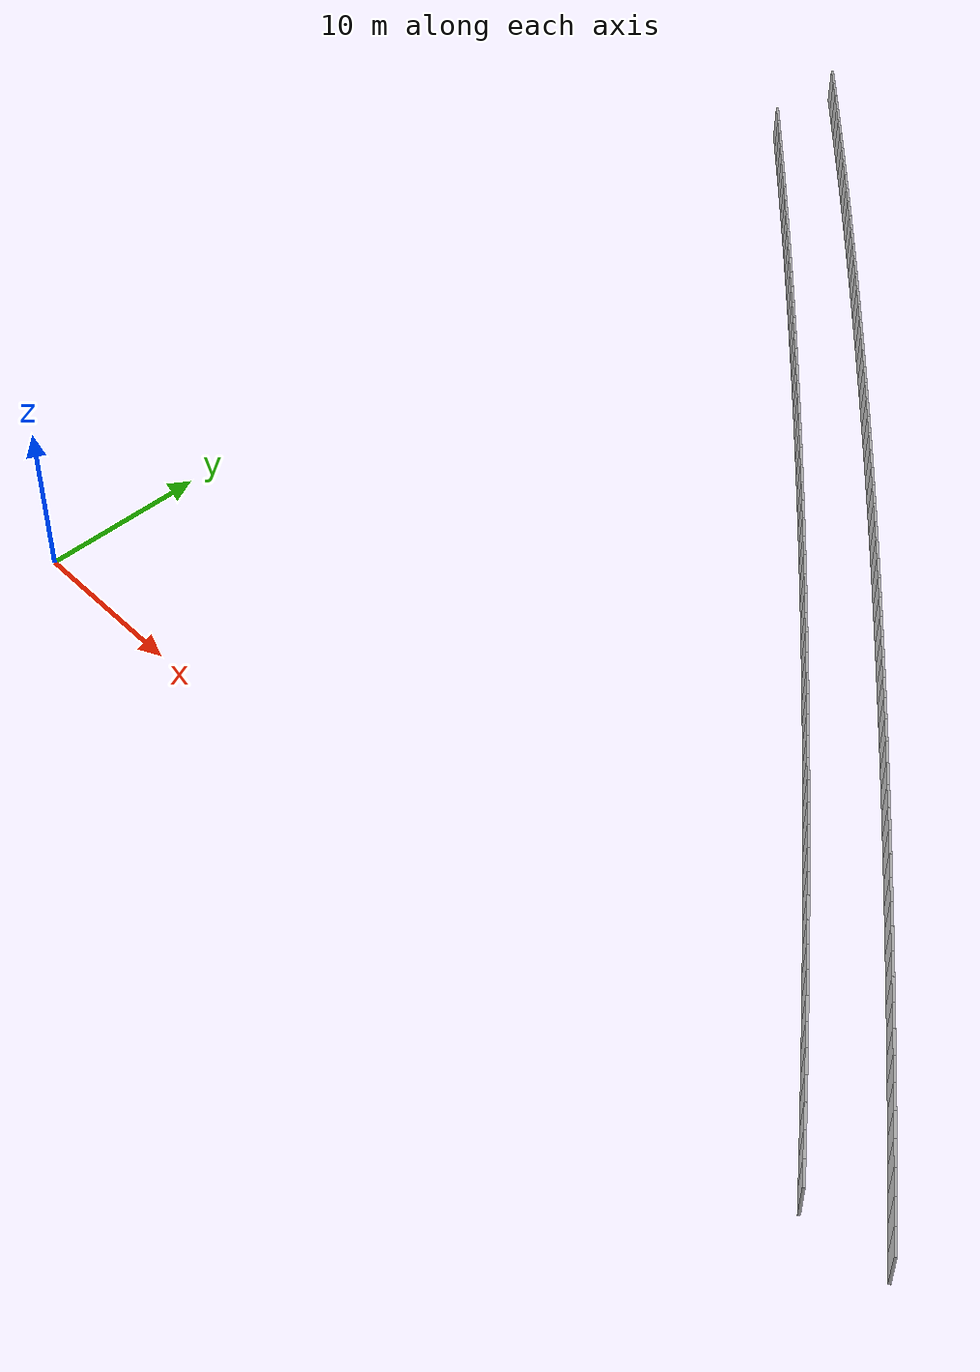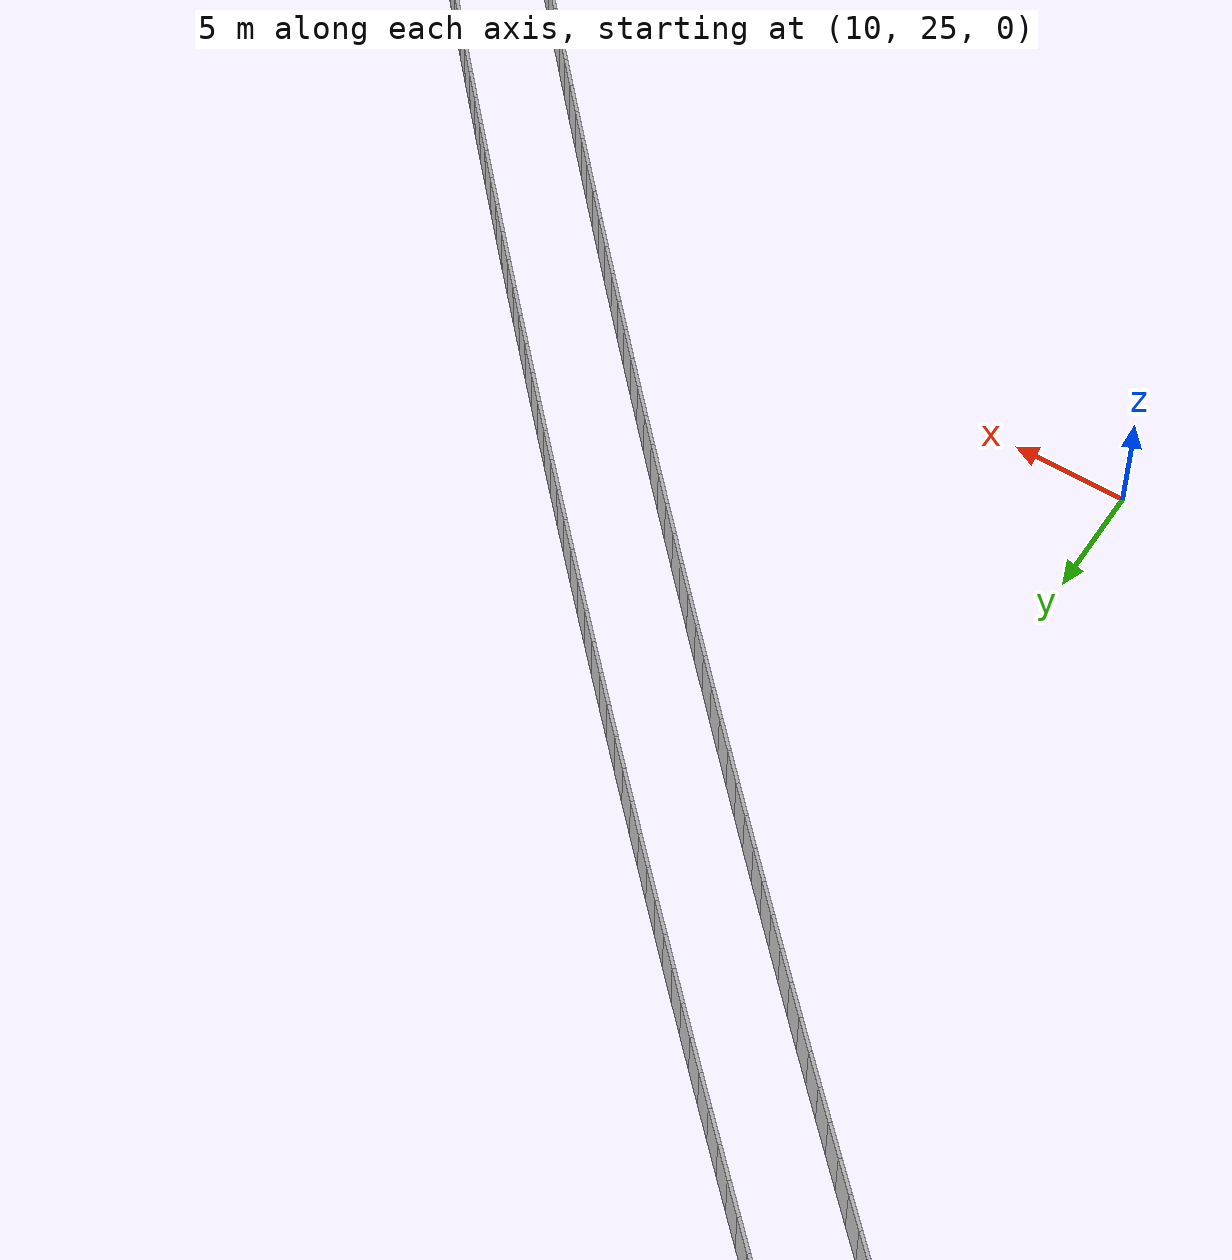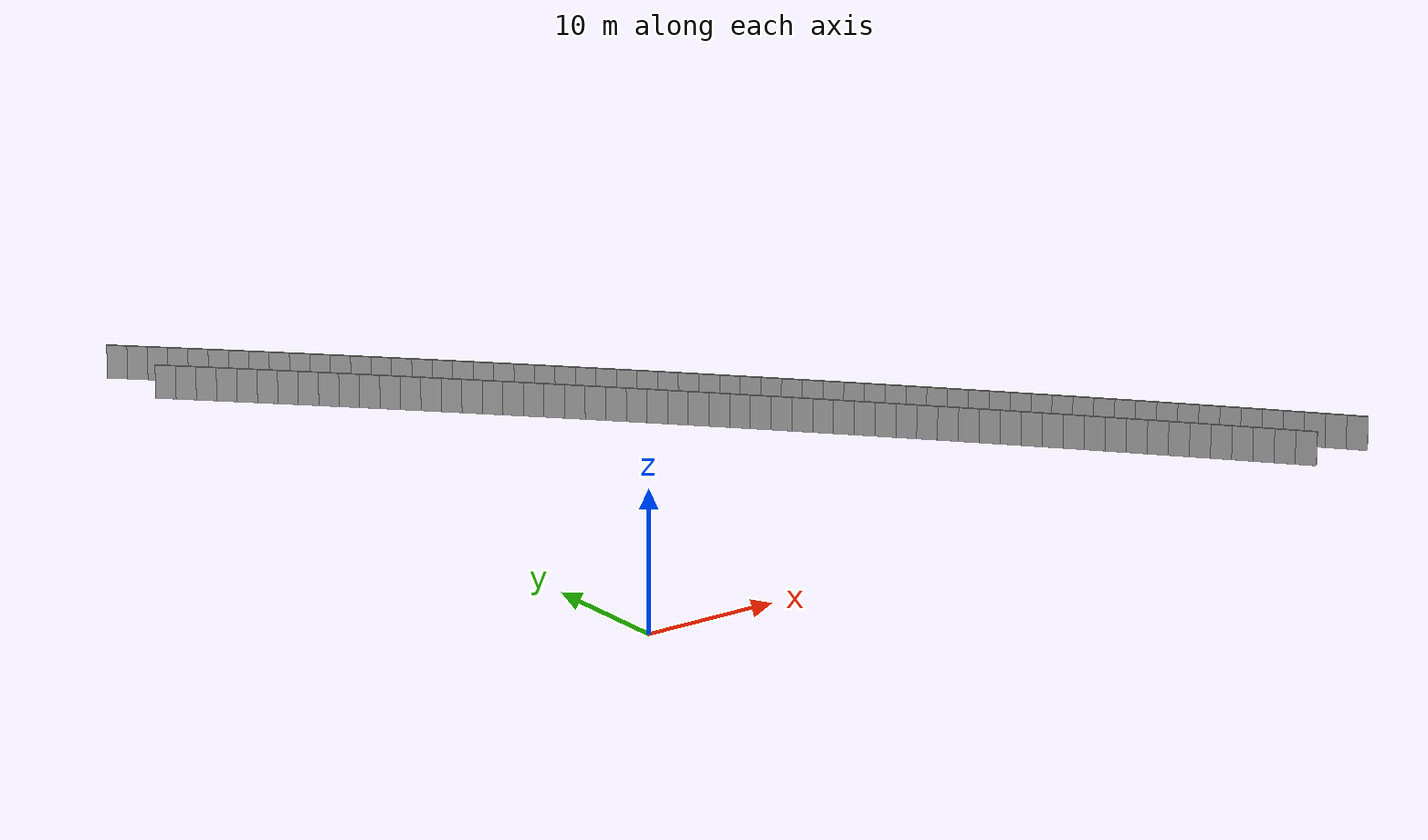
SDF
<?xml version="1.0" ?>
<sdf version="1.6">
  <model name="sps_2020">
    <pose frame="">0 0 0 0 -0 0</pose>
    <static>1</static>
    <self_collide>0</self_collide>
    <allow_auto_disable>0</allow_auto_disable>
    <link name="Wall10409">
      <kinematic>0</kinematic>
      <gravity>1</gravity>
      <self_collide>0</self_collide>
      <collision name="collision">
        <geometry>
          <box>
            <size>1.4966 0.15 2.5</size>
          </box>
        </geometry>
        <pose frame="">0 0 0 0 -0 0</pose>
      </collision>
      <visual name="visual">
        <geometry>
          <box>
            <size>1.4966 0.15 2.5</size>
          </box>
        </geometry>
        <pose frame="">0 0 0 0 -0 0</pose>
        <cast_shadows>1</cast_shadows>
        <transparency>0.0</transparency>
      </visual>
      <pose frame="">57.1239 0.688186 1.25 0 -0 2.27912</pose>
    </link>
    <link name="Wall10410">
      <kinematic>0</kinematic>
      <gravity>1</gravity>
      <self_collide>0</self_collide>
      <collision name="collision">
        <geometry>
          <box>
            <size>1.49655 0.15 2.5</size>
          </box>
        </geometry>
        <pose frame="">0 0 0 0 -0 0</pose>
      </collision>
      <visual name="visual">
        <geometry>
          <box>
            <size>1.49655 0.15 2.5</size>
          </box>
        </geometry>
        <pose frame="">0 0 0 0 -0 0</pose>
        <cast_shadows>1</cast_shadows>
        <transparency>0.0</transparency>
      </visual>
      <pose frame="">56.1493 1.82399 1.25 0 -0 2.28071</pose>
    </link>
    <link name="Wall10411">
      <kinematic>0</kinematic>
      <gravity>1</gravity>
      <self_collide>0</self_collide>
      <collision name="collision">
        <geometry>
          <box>
            <size>1.49638 0.15 2.5</size>
          </box>
        </geometry>
        <pose frame="">0 0 0 0 -0 0</pose>
      </collision>
      <visual name="visual">
        <geometry>
          <box>
            <size>1.49638 0.15 2.5</size>
          </box>
        </geometry>
        <pose frame="">0 0 0 0 -0 0</pose>
        <cast_shadows>1</cast_shadows>
        <transparency>0.0</transparency>
      </visual>
      <pose frame="">55.1731 2.95821 1.25 0 -0 2.28221</pose>
    </link>
    <link name="Wall10412">
      <kinematic>0</kinematic>
      <gravity>1</gravity>
      <self_collide>0</self_collide>
      <collision name="collision">
        <geometry>
          <box>
            <size>1.49645 0.15 2.5</size>
          </box>
        </geometry>
        <pose frame="">0 0 0 0 -0 0</pose>
      </collision>
      <visual name="visual">
        <geometry>
          <box>
            <size>1.49645 0.15 2.5</size>
          </box>
        </geometry>
        <pose frame="">0 0 0 0 -0 0</pose>
        <cast_shadows>1</cast_shadows>
        <transparency>0.0</transparency>
      </visual>
      <pose frame="">54.1952 4.0908 1.25 0 -0 2.28394</pose>
    </link>
    <link name="Wall10413">
      <kinematic>0</kinematic>
      <gravity>1</gravity>
      <self_collide>0</self_collide>
      <collision name="collision">
        <geometry>
          <box>
            <size>1.49655 0.15 2.5</size>
          </box>
        </geometry>
        <pose frame="">0 0 0 0 -0 0</pose>
      </collision>
      <visual name="visual">
        <geometry>
          <box>
            <size>1.49655 0.15 2.5</size>
          </box>
        </geometry>
        <pose frame="">0 0 0 0 -0 0</pose>
        <cast_shadows>1</cast_shadows>
        <transparency>0.0</transparency>
      </visual>
      <pose frame="">53.2153 5.22188 1.25 0 -0 2.28545</pose>
    </link>
    <link name="Wall10414">
      <kinematic>0</kinematic>
      <gravity>1</gravity>
      <self_collide>0</self_collide>
      <collision name="collision">
        <geometry>
          <box>
            <size>1.49648 0.15 2.5</size>
          </box>
        </geometry>
        <pose frame="">0 0 0 0 -0 0</pose>
      </collision>
      <visual name="visual">
        <geometry>
          <box>
            <size>1.49648 0.15 2.5</size>
          </box>
        </geometry>
        <pose frame="">0 0 0 0 -0 0</pose>
        <cast_shadows>1</cast_shadows>
        <transparency>0.0</transparency>
      </visual>
      <pose frame="">52.2337 6.35149 1.25 0 -0 2.28695</pose>
    </link>
    <link name="Wall10415">
      <kinematic>0</kinematic>
      <gravity>1</gravity>
      <self_collide>0</self_collide>
      <collision name="collision">
        <geometry>
          <box>
            <size>1.49652 0.15 2.5</size>
          </box>
        </geometry>
        <pose frame="">0 0 0 0 -0 0</pose>
      </collision>
      <visual name="visual">
        <geometry>
          <box>
            <size>1.49652 0.15 2.5</size>
          </box>
        </geometry>
        <pose frame="">0 0 0 0 -0 0</pose>
        <cast_shadows>1</cast_shadows>
        <transparency>0.0</transparency>
      </visual>
      <pose frame="">51.2503 7.47951 1.25 0 -0 2.28866</pose>
    </link>
    <link name="Wall10416">
      <kinematic>0</kinematic>
      <gravity>1</gravity>
      <self_collide>0</self_collide>
      <collision name="collision">
        <geometry>
          <box>
            <size>1.49667 0.15 2.5</size>
          </box>
        </geometry>
        <pose frame="">0 0 0 0 -0 0</pose>
      </collision>
      <visual name="visual">
        <geometry>
          <box>
            <size>1.49667 0.15 2.5</size>
          </box>
        </geometry>
        <pose frame="">0 0 0 0 -0 0</pose>
        <cast_shadows>1</cast_shadows>
        <transparency>0.0</transparency>
      </visual>
      <pose frame="">50.265 8.606 1.25 0 -0 2.2902</pose>
    </link>
    <link name="Wall10417">
      <kinematic>0</kinematic>
      <gravity>1</gravity>
      <self_collide>0</self_collide>
      <collision name="collision">
        <geometry>
          <box>
            <size>1.49638 0.15 2.5</size>
          </box>
        </geometry>
        <pose frame="">0 0 0 0 -0 0</pose>
      </collision>
      <visual name="visual">
        <geometry>
          <box>
            <size>1.49638 0.15 2.5</size>
          </box>
        </geometry>
        <pose frame="">0 0 0 0 -0 0</pose>
        <cast_shadows>1</cast_shadows>
        <transparency>0.0</transparency>
      </visual>
      <pose frame="">49.278 9.73091 1.25 0 -0 2.29178</pose>
    </link>
    <link name="Wall10418">
      <kinematic>0</kinematic>
      <gravity>1</gravity>
      <self_collide>0</self_collide>
      <collision name="collision">
        <geometry>
          <box>
            <size>1.49661 0.15 2.5</size>
          </box>
        </geometry>
        <pose frame="">0 0 0 0 -0 0</pose>
      </collision>
      <visual name="visual">
        <geometry>
          <box>
            <size>1.49661 0.15 2.5</size>
          </box>
        </geometry>
        <pose frame="">0 0 0 0 -0 0</pose>
        <cast_shadows>1</cast_shadows>
        <transparency>0.0</transparency>
      </visual>
      <pose frame="">48.2892 10.8542 1.25 0 -0 2.29343</pose>
    </link>
    <link name="Wall10419">
      <kinematic>0</kinematic>
      <gravity>1</gravity>
      <self_collide>0</self_collide>
      <collision name="collision">
        <geometry>
          <box>
            <size>1.49652 0.15 2.5</size>
          </box>
        </geometry>
        <pose frame="">0 0 0 0 -0 0</pose>
      </collision>
      <visual name="visual">
        <geometry>
          <box>
            <size>1.49652 0.15 2.5</size>
          </box>
        </geometry>
        <pose frame="">0 0 0 0 -0 0</pose>
        <cast_shadows>1</cast_shadows>
        <transparency>0.0</transparency>
      </visual>
      <pose frame="">47.2986 11.976 1.25 0 -0 2.2949</pose>
    </link>
    <link name="Wall10420">
      <kinematic>0</kinematic>
      <gravity>1</gravity>
      <self_collide>0</self_collide>
      <collision name="collision">
        <geometry>
          <box>
            <size>1.4965 0.15 2.5</size>
          </box>
        </geometry>
        <pose frame="">0 0 0 0 -0 0</pose>
      </collision>
      <visual name="visual">
        <geometry>
          <box>
            <size>1.4965 0.15 2.5</size>
          </box>
        </geometry>
        <pose frame="">0 0 0 0 -0 0</pose>
        <cast_shadows>1</cast_shadows>
        <transparency>0.0</transparency>
      </visual>
      <pose frame="">46.3063 13.0962 1.25 0 -0 2.29655</pose>
    </link>
    <link name="Wall10421">
      <kinematic>0</kinematic>
      <gravity>1</gravity>
      <self_collide>0</self_collide>
      <collision name="collision">
        <geometry>
          <box>
            <size>1.49649 0.15 2.5</size>
          </box>
        </geometry>
        <pose frame="">0 0 0 0 -0 0</pose>
      </collision>
      <visual name="visual">
        <geometry>
          <box>
            <size>1.49649 0.15 2.5</size>
          </box>
        </geometry>
        <pose frame="">0 0 0 0 -0 0</pose>
        <cast_shadows>1</cast_shadows>
        <transparency>0.0</transparency>
      </visual>
      <pose frame="">45.3122 14.2148 1.25 0 -0 2.29814</pose>
    </link>
    <link name="Wall10422">
      <kinematic>0</kinematic>
      <gravity>1</gravity>
      <self_collide>0</self_collide>
      <collision name="collision">
        <geometry>
          <box>
            <size>1.49621 0.15 2.5</size>
          </box>
        </geometry>
        <pose frame="">0 0 0 0 -0 0</pose>
      </collision>
      <visual name="visual">
        <geometry>
          <box>
            <size>1.49621 0.15 2.5</size>
          </box>
        </geometry>
        <pose frame="">0 0 0 0 -0 0</pose>
        <cast_shadows>1</cast_shadows>
        <transparency>0.0</transparency>
      </visual>
      <pose frame="">44.3162 15.3316 1.25 0 -0 2.29995</pose>
    </link>
    <link name="Wall10423">
      <kinematic>0</kinematic>
      <gravity>1</gravity>
      <self_collide>0</self_collide>
      <collision name="collision">
        <geometry>
          <box>
            <size>1.49666 0.15 2.5</size>
          </box>
        </geometry>
        <pose frame="">0 0 0 0 -0 0</pose>
      </collision>
      <visual name="visual">
        <geometry>
          <box>
            <size>1.49666 0.15 2.5</size>
          </box>
        </geometry>
        <pose frame="">0 0 0 0 -0 0</pose>
        <cast_shadows>1</cast_shadows>
        <transparency>0.0</transparency>
      </visual>
      <pose frame="">43.3185 16.4469 1.25 0 -0 2.30126</pose>
    </link>
    <link name="Wall10424">
      <kinematic>0</kinematic>
      <gravity>1</gravity>
      <self_collide>0</self_collide>
      <collision name="collision">
        <geometry>
          <box>
            <size>1.49636 0.15 2.5</size>
          </box>
        </geometry>
        <pose frame="">0 0 0 0 -0 0</pose>
      </collision>
      <visual name="visual">
        <geometry>
          <box>
            <size>1.49636 0.15 2.5</size>
          </box>
        </geometry>
        <pose frame="">0 0 0 0 -0 0</pose>
        <cast_shadows>1</cast_shadows>
        <transparency>0.0</transparency>
      </visual>
      <pose frame="">42.3191 17.5608 1.25 0 -0 2.30287</pose>
    </link>
    <link name="Wall10425">
      <kinematic>0</kinematic>
      <gravity>1</gravity>
      <self_collide>0</self_collide>
      <collision name="collision">
        <geometry>
          <box>
            <size>1.49658 0.15 2.5</size>
          </box>
        </geometry>
        <pose frame="">0 0 0 0 -0 0</pose>
      </collision>
      <visual name="visual">
        <geometry>
          <box>
            <size>1.49658 0.15 2.5</size>
          </box>
        </geometry>
        <pose frame="">0 0 0 0 -0 0</pose>
        <cast_shadows>1</cast_shadows>
        <transparency>0.0</transparency>
      </visual>
      <pose frame="">41.318 18.6731 1.25 0 -0 2.30438</pose>
    </link>
    <link name="Wall10426">
      <kinematic>0</kinematic>
      <gravity>1</gravity>
      <self_collide>0</self_collide>
      <collision name="collision">
        <geometry>
          <box>
            <size>1.49655 0.15 2.5</size>
          </box>
        </geometry>
        <pose frame="">0 0 0 0 -0 0</pose>
      </collision>
      <visual name="visual">
        <geometry>
          <box>
            <size>1.49655 0.15 2.5</size>
          </box>
        </geometry>
        <pose frame="">0 0 0 0 -0 0</pose>
        <cast_shadows>1</cast_shadows>
        <transparency>0.0</transparency>
      </visual>
      <pose frame="">40.3151 19.7839 1.25 0 -0 2.30599</pose>
    </link>
    <link name="Wall10427">
      <kinematic>0</kinematic>
      <gravity>1</gravity>
      <self_collide>0</self_collide>
      <collision name="collision">
        <geometry>
          <box>
            <size>1.49646 0.15 2.5</size>
          </box>
        </geometry>
        <pose frame="">0 0 0 0 -0 0</pose>
      </collision>
      <visual name="visual">
        <geometry>
          <box>
            <size>1.49646 0.15 2.5</size>
          </box>
        </geometry>
        <pose frame="">0 0 0 0 -0 0</pose>
        <cast_shadows>1</cast_shadows>
        <transparency>0.0</transparency>
      </visual>
      <pose frame="">39.3104 20.893 1.25 0 -0 2.3077</pose>
    </link>
    <link name="Wall10428">
      <kinematic>0</kinematic>
      <gravity>1</gravity>
      <self_collide>0</self_collide>
      <collision name="collision">
        <geometry>
          <box>
            <size>1.49662 0.15 2.5</size>
          </box>
        </geometry>
        <pose frame="">0 0 0 0 -0 0</pose>
      </collision>
      <visual name="visual">
        <geometry>
          <box>
            <size>1.49662 0.15 2.5</size>
          </box>
        </geometry>
        <pose frame="">0 0 0 0 -0 0</pose>
        <cast_shadows>1</cast_shadows>
        <transparency>0.0</transparency>
      </visual>
      <pose frame="">38.3039 22.0005 1.25 0 -0 2.3092</pose>
    </link>
    <link name="Wall10429">
      <kinematic>0</kinematic>
      <gravity>1</gravity>
      <self_collide>0</self_collide>
      <collision name="collision">
        <geometry>
          <box>
            <size>1.4965 0.15 2.5</size>
          </box>
        </geometry>
        <pose frame="">0 0 0 0 -0 0</pose>
      </collision>
      <visual name="visual">
        <geometry>
          <box>
            <size>1.4965 0.15 2.5</size>
          </box>
        </geometry>
        <pose frame="">0 0 0 0 -0 0</pose>
        <cast_shadows>1</cast_shadows>
        <transparency>0.0</transparency>
      </visual>
      <pose frame="">37.2956 23.1064 1.25 0 -0 2.31093</pose>
    </link>
    <link name="Wall10430">
      <kinematic>0</kinematic>
      <gravity>1</gravity>
      <self_collide>0</self_collide>
      <collision name="collision">
        <geometry>
          <box>
            <size>1.49653 0.15 2.5</size>
          </box>
        </geometry>
        <pose frame="">0 0 0 0 -0 0</pose>
      </collision>
      <visual name="visual">
        <geometry>
          <box>
            <size>1.49653 0.15 2.5</size>
          </box>
        </geometry>
        <pose frame="">0 0 0 0 -0 0</pose>
        <cast_shadows>1</cast_shadows>
        <transparency>0.0</transparency>
      </visual>
      <pose frame="">36.2856 24.2107 1.25 0 -0 2.31235</pose>
    </link>
    <link name="Wall10431">
      <kinematic>0</kinematic>
      <gravity>1</gravity>
      <self_collide>0</self_collide>
      <collision name="collision">
        <geometry>
          <box>
            <size>1.49642 0.15 2.5</size>
          </box>
        </geometry>
        <pose frame="">0 0 0 0 -0 0</pose>
      </collision>
      <visual name="visual">
        <geometry>
          <box>
            <size>1.49642 0.15 2.5</size>
          </box>
        </geometry>
        <pose frame="">0 0 0 0 -0 0</pose>
        <cast_shadows>1</cast_shadows>
        <transparency>0.0</transparency>
      </visual>
      <pose frame="">35.2739 25.3134 1.25 0 -0 2.31402</pose>
    </link>
    <link name="Wall10432">
      <kinematic>0</kinematic>
      <gravity>1</gravity>
      <self_collide>0</self_collide>
      <collision name="collision">
        <geometry>
          <box>
            <size>1.49651 0.15 2.5</size>
          </box>
        </geometry>
        <pose frame="">0 0 0 0 -0 0</pose>
      </collision>
      <visual name="visual">
        <geometry>
          <box>
            <size>1.49651 0.15 2.5</size>
          </box>
        </geometry>
        <pose frame="">0 0 0 0 -0 0</pose>
        <cast_shadows>1</cast_shadows>
        <transparency>0.0</transparency>
      </visual>
      <pose frame="">34.2606 26.4145 1.25 0 -0 2.31546</pose>
    </link>
    <link name="Wall10433">
      <kinematic>0</kinematic>
      <gravity>1</gravity>
      <self_collide>0</self_collide>
      <collision name="collision">
        <geometry>
          <box>
            <size>1.49653 0.15 2.5</size>
          </box>
        </geometry>
        <pose frame="">0 0 0 0 -0 0</pose>
      </collision>
      <visual name="visual">
        <geometry>
          <box>
            <size>1.49653 0.15 2.5</size>
          </box>
        </geometry>
        <pose frame="">0 0 0 0 -0 0</pose>
        <cast_shadows>1</cast_shadows>
        <transparency>0.0</transparency>
      </visual>
      <pose frame="">33.2454 27.514 1.25 0 -0 2.31722</pose>
    </link>
    <link name="Wall10434">
      <kinematic>0</kinematic>
      <gravity>1</gravity>
      <self_collide>0</self_collide>
      <collision name="collision">
        <geometry>
          <box>
            <size>1.49658 0.15 2.5</size>
          </box>
        </geometry>
        <pose frame="">0 0 0 0 -0 0</pose>
      </collision>
      <visual name="visual">
        <geometry>
          <box>
            <size>1.49658 0.15 2.5</size>
          </box>
        </geometry>
        <pose frame="">0 0 0 0 -0 0</pose>
        <cast_shadows>1</cast_shadows>
        <transparency>0.0</transparency>
      </visual>
      <pose frame="">32.2284 28.6119 1.25 0 -0 2.3187</pose>
    </link>
    <link name="Wall10435">
      <kinematic>0</kinematic>
      <gravity>1</gravity>
      <self_collide>0</self_collide>
      <collision name="collision">
        <geometry>
          <box>
            <size>1.49636 0.15 2.5</size>
          </box>
        </geometry>
        <pose frame="">0 0 0 0 -0 0</pose>
      </collision>
      <visual name="visual">
        <geometry>
          <box>
            <size>1.49636 0.15 2.5</size>
          </box>
        </geometry>
        <pose frame="">0 0 0 0 -0 0</pose>
        <cast_shadows>1</cast_shadows>
        <transparency>0.0</transparency>
      </visual>
      <pose frame="">31.2097 29.7082 1.25 0 -0 2.32028</pose>
    </link>
    <link name="Wall10436">
      <kinematic>0</kinematic>
      <gravity>1</gravity>
      <self_collide>0</self_collide>
      <collision name="collision">
        <geometry>
          <box>
            <size>1.49666 0.15 2.5</size>
          </box>
        </geometry>
        <pose frame="">0 0 0 0 -0 0</pose>
      </collision>
      <visual name="visual">
        <geometry>
          <box>
            <size>1.49666 0.15 2.5</size>
          </box>
        </geometry>
        <pose frame="">0 0 0 0 -0 0</pose>
        <cast_shadows>1</cast_shadows>
        <transparency>0.0</transparency>
      </visual>
      <pose frame="">30.1894 30.8029 1.25 0 -0 2.32187</pose>
    </link>
    <link name="Wall10437">
      <kinematic>0</kinematic>
      <gravity>1</gravity>
      <self_collide>0</self_collide>
      <collision name="collision">
        <geometry>
          <box>
            <size>1.49637 0.15 2.5</size>
          </box>
        </geometry>
        <pose frame="">0 0 0 0 -0 0</pose>
      </collision>
      <visual name="visual">
        <geometry>
          <box>
            <size>1.49637 0.15 2.5</size>
          </box>
        </geometry>
        <pose frame="">0 0 0 0 -0 0</pose>
        <cast_shadows>1</cast_shadows>
        <transparency>0.0</transparency>
      </visual>
      <pose frame="">29.1673 31.896 1.25 0 -0 2.3234</pose>
    </link>
    <link name="Wall10438">
      <kinematic>0</kinematic>
      <gravity>1</gravity>
      <self_collide>0</self_collide>
      <collision name="collision">
        <geometry>
          <box>
            <size>1.49651 0.15 2.5</size>
          </box>
        </geometry>
        <pose frame="">0 0 0 0 -0 0</pose>
      </collision>
      <visual name="visual">
        <geometry>
          <box>
            <size>1.49651 0.15 2.5</size>
          </box>
        </geometry>
        <pose frame="">0 0 0 0 -0 0</pose>
        <cast_shadows>1</cast_shadows>
        <transparency>0.0</transparency>
      </visual>
      <pose frame="">28.1435 32.9874 1.25 0 -0 2.3251</pose>
    </link>
    <link name="Wall10439">
      <kinematic>0</kinematic>
      <gravity>1</gravity>
      <self_collide>0</self_collide>
      <collision name="collision">
        <geometry>
          <box>
            <size>1.49652 0.15 2.5</size>
          </box>
        </geometry>
        <pose frame="">0 0 0 0 -0 0</pose>
      </collision>
      <visual name="visual">
        <geometry>
          <box>
            <size>1.49652 0.15 2.5</size>
          </box>
        </geometry>
        <pose frame="">0 0 0 0 -0 0</pose>
        <cast_shadows>1</cast_shadows>
        <transparency>0.0</transparency>
      </visual>
      <pose frame="">27.1179 34.0772 1.25 0 -0 2.3266</pose>
    </link>
    <link name="Wall10440">
      <kinematic>0</kinematic>
      <gravity>1</gravity>
      <self_collide>0</self_collide>
      <collision name="collision">
        <geometry>
          <box>
            <size>1.49636 0.15 2.5</size>
          </box>
        </geometry>
        <pose frame="">0 0 0 0 -0 0</pose>
      </collision>
      <visual name="visual">
        <geometry>
          <box>
            <size>1.49636 0.15 2.5</size>
          </box>
        </geometry>
        <pose frame="">0 0 0 0 -0 0</pose>
        <cast_shadows>1</cast_shadows>
        <transparency>0.0</transparency>
      </visual>
      <pose frame="">26.0905 35.1653 1.25 0 -0 2.32833</pose>
    </link>
    <link name="Wall10441">
      <kinematic>0</kinematic>
      <gravity>1</gravity>
      <self_collide>0</self_collide>
      <collision name="collision">
        <geometry>
          <box>
            <size>1.49674 0.15 2.5</size>
          </box>
        </geometry>
        <pose frame="">0 0 0 0 -0 0</pose>
      </collision>
      <visual name="visual">
        <geometry>
          <box>
            <size>1.49674 0.15 2.5</size>
          </box>
        </geometry>
        <pose frame="">0 0 0 0 -0 0</pose>
        <cast_shadows>1</cast_shadows>
        <transparency>0.0</transparency>
      </visual>
      <pose frame="">25.0615 36.2519 1.25 0 -0 2.32972</pose>
    </link>
    <link name="Wall10442">
      <kinematic>0</kinematic>
      <gravity>1</gravity>
      <self_collide>0</self_collide>
      <collision name="collision">
        <geometry>
          <box>
            <size>1.49646 0.15 2.5</size>
          </box>
        </geometry>
        <pose frame="">0 0 0 0 -0 0</pose>
      </collision>
      <visual name="visual">
        <geometry>
          <box>
            <size>1.49646 0.15 2.5</size>
          </box>
        </geometry>
        <pose frame="">0 0 0 0 -0 0</pose>
        <cast_shadows>1</cast_shadows>
        <transparency>0.0</transparency>
      </visual>
      <pose frame="">24.0307 37.3369 1.25 0 -0 2.33142</pose>
    </link>
    <link name="Wall10443">
      <kinematic>0</kinematic>
      <gravity>1</gravity>
      <self_collide>0</self_collide>
      <collision name="collision">
        <geometry>
          <box>
            <size>1.49662 0.15 2.5</size>
          </box>
        </geometry>
        <pose frame="">0 0 0 0 -0 0</pose>
      </collision>
      <visual name="visual">
        <geometry>
          <box>
            <size>1.49662 0.15 2.5</size>
          </box>
        </geometry>
        <pose frame="">0 0 0 0 -0 0</pose>
        <cast_shadows>1</cast_shadows>
        <transparency>0.0</transparency>
      </visual>
      <pose frame="">22.9982 38.4202 1.25 0 -0 2.33295</pose>
    </link>
    <link name="Wall10444">
      <kinematic>0</kinematic>
      <gravity>1</gravity>
      <self_collide>0</self_collide>
      <collision name="collision">
        <geometry>
          <box>
            <size>1.49661 0.15 2.5</size>
          </box>
        </geometry>
        <pose frame="">0 0 0 0 -0 0</pose>
      </collision>
      <visual name="visual">
        <geometry>
          <box>
            <size>1.49661 0.15 2.5</size>
          </box>
        </geometry>
        <pose frame="">0 0 0 0 -0 0</pose>
        <cast_shadows>1</cast_shadows>
        <transparency>0.0</transparency>
      </visual>
      <pose frame="">21.964 39.502 1.25 0 -0 2.33448</pose>
    </link>
    <link name="Wall10445">
      <kinematic>0</kinematic>
      <gravity>1</gravity>
      <self_collide>0</self_collide>
      <collision name="collision">
        <geometry>
          <box>
            <size>1.49656 0.15 2.5</size>
          </box>
        </geometry>
        <pose frame="">0 0 0 0 -0 0</pose>
      </collision>
      <visual name="visual">
        <geometry>
          <box>
            <size>1.49656 0.15 2.5</size>
          </box>
        </geometry>
        <pose frame="">0 0 0 0 -0 0</pose>
        <cast_shadows>1</cast_shadows>
        <transparency>0.0</transparency>
      </visual>
      <pose frame="">20.928 40.5821 1.25 0 -0 2.33615</pose>
    </link>
    <link name="Wall10446">
      <kinematic>0</kinematic>
      <gravity>1</gravity>
      <self_collide>0</self_collide>
      <collision name="collision">
        <geometry>
          <box>
            <size>1.49634 0.15 2.5</size>
          </box>
        </geometry>
        <pose frame="">0 0 0 0 -0 0</pose>
      </collision>
      <visual name="visual">
        <geometry>
          <box>
            <size>1.49634 0.15 2.5</size>
          </box>
        </geometry>
        <pose frame="">0 0 0 0 -0 0</pose>
        <cast_shadows>1</cast_shadows>
        <transparency>0.0</transparency>
      </visual>
      <pose frame="">19.8904 41.6604 1.25 0 -0 2.33776</pose>
    </link>
    <link name="Wall10447">
      <kinematic>0</kinematic>
      <gravity>1</gravity>
      <self_collide>0</self_collide>
      <collision name="collision">
        <geometry>
          <box>
            <size>1.49656 0.15 2.5</size>
          </box>
        </geometry>
        <pose frame="">0 0 0 0 -0 0</pose>
      </collision>
      <visual name="visual">
        <geometry>
          <box>
            <size>1.49656 0.15 2.5</size>
          </box>
        </geometry>
        <pose frame="">0 0 0 0 -0 0</pose>
        <cast_shadows>1</cast_shadows>
        <transparency>0.0</transparency>
      </visual>
      <pose frame="">18.8512 42.7371 1.25 0 -0 2.33927</pose>
    </link>
    <link name="Wall10448">
      <kinematic>0</kinematic>
      <gravity>1</gravity>
      <self_collide>0</self_collide>
      <collision name="collision">
        <geometry>
          <box>
            <size>1.49643 0.15 2.5</size>
          </box>
        </geometry>
        <pose frame="">0 0 0 0 -0 0</pose>
      </collision>
      <visual name="visual">
        <geometry>
          <box>
            <size>1.49643 0.15 2.5</size>
          </box>
        </geometry>
        <pose frame="">0 0 0 0 -0 0</pose>
        <cast_shadows>1</cast_shadows>
        <transparency>0.0</transparency>
      </visual>
      <pose frame="">17.8102 43.8122 1.25 0 -0 2.34088</pose>
    </link>
    <link name="Wall10449">
      <kinematic>0</kinematic>
      <gravity>1</gravity>
      <self_collide>0</self_collide>
      <collision name="collision">
        <geometry>
          <box>
            <size>1.4964 0.15 2.5</size>
          </box>
        </geometry>
        <pose frame="">0 0 0 0 -0 0</pose>
      </collision>
      <visual name="visual">
        <geometry>
          <box>
            <size>1.4964 0.15 2.5</size>
          </box>
        </geometry>
        <pose frame="">0 0 0 0 -0 0</pose>
        <cast_shadows>1</cast_shadows>
        <transparency>0.0</transparency>
      </visual>
      <pose frame="">16.7674 44.8855 1.25 0 -0 2.34261</pose>
    </link>
    <link name="Wall10450">
      <kinematic>0</kinematic>
      <gravity>1</gravity>
      <self_collide>0</self_collide>
      <collision name="collision">
        <geometry>
          <box>
            <size>1.49658 0.15 2.5</size>
          </box>
        </geometry>
        <pose frame="">0 0 0 0 -0 0</pose>
      </collision>
      <visual name="visual">
        <geometry>
          <box>
            <size>1.49658 0.15 2.5</size>
          </box>
        </geometry>
        <pose frame="">0 0 0 0 -0 0</pose>
        <cast_shadows>1</cast_shadows>
        <transparency>0.0</transparency>
      </visual>
      <pose frame="">15.723 45.9572 1.25 0 -0 2.34408</pose>
    </link>
    <link name="Wall10451">
      <kinematic>0</kinematic>
      <gravity>1</gravity>
      <self_collide>0</self_collide>
      <collision name="collision">
        <geometry>
          <box>
            <size>1.4966 0.15 2.5</size>
          </box>
        </geometry>
        <pose frame="">0 0 0 0 -0 0</pose>
      </collision>
      <visual name="visual">
        <geometry>
          <box>
            <size>1.4966 0.15 2.5</size>
          </box>
        </geometry>
        <pose frame="">0 0 0 0 -0 0</pose>
        <cast_shadows>1</cast_shadows>
        <transparency>0.0</transparency>
      </visual>
      <pose frame="">14.6768 47.0274 1.25 0 -0 2.34561</pose>
    </link>
    <link name="Wall10452">
      <kinematic>0</kinematic>
      <gravity>1</gravity>
      <self_collide>0</self_collide>
      <collision name="collision">
        <geometry>
          <box>
            <size>1.49649 0.15 2.5</size>
          </box>
        </geometry>
        <pose frame="">0 0 0 0 -0 0</pose>
      </collision>
      <visual name="visual">
        <geometry>
          <box>
            <size>1.49649 0.15 2.5</size>
          </box>
        </geometry>
        <pose frame="">0 0 0 0 -0 0</pose>
        <cast_shadows>1</cast_shadows>
        <transparency>0.0</transparency>
      </visual>
      <pose frame="">13.629 48.0959 1.25 0 -0 2.34723</pose>
    </link>
    <link name="Wall10453">
      <kinematic>0</kinematic>
      <gravity>1</gravity>
      <self_collide>0</self_collide>
      <collision name="collision">
        <geometry>
          <box>
            <size>1.49638 0.15 2.5</size>
          </box>
        </geometry>
        <pose frame="">0 0 0 0 -0 0</pose>
      </collision>
      <visual name="visual">
        <geometry>
          <box>
            <size>1.49638 0.15 2.5</size>
          </box>
        </geometry>
        <pose frame="">0 0 0 0 -0 0</pose>
        <cast_shadows>1</cast_shadows>
        <transparency>0.0</transparency>
      </visual>
      <pose frame="">12.5795 49.1626 1.25 0 -0 2.3489</pose>
    </link>
    <link name="Wall10454">
      <kinematic>0</kinematic>
      <gravity>1</gravity>
      <self_collide>0</self_collide>
      <collision name="collision">
        <geometry>
          <box>
            <size>1.49671 0.15 2.5</size>
          </box>
        </geometry>
        <pose frame="">0 0 0 0 -0 0</pose>
      </collision>
      <visual name="visual">
        <geometry>
          <box>
            <size>1.49671 0.15 2.5</size>
          </box>
        </geometry>
        <pose frame="">0 0 0 0 -0 0</pose>
        <cast_shadows>1</cast_shadows>
        <transparency>0.0</transparency>
      </visual>
      <pose frame="">11.5282 50.2277 1.25 0 -0 2.35046</pose>
    </link>
    <link name="Wall10455">
      <kinematic>0</kinematic>
      <gravity>1</gravity>
      <self_collide>0</self_collide>
      <collision name="collision">
        <geometry>
          <box>
            <size>1.49636 0.15 2.5</size>
          </box>
        </geometry>
        <pose frame="">0 0 0 0 -0 0</pose>
      </collision>
      <visual name="visual">
        <geometry>
          <box>
            <size>1.49636 0.15 2.5</size>
          </box>
        </geometry>
        <pose frame="">0 0 0 0 -0 0</pose>
        <cast_shadows>1</cast_shadows>
        <transparency>0.0</transparency>
      </visual>
      <pose frame="">10.4752 51.2911 1.25 0 -0 2.35213</pose>
    </link>
    <link name="Wall10456">
      <kinematic>0</kinematic>
      <gravity>1</gravity>
      <self_collide>0</self_collide>
      <collision name="collision">
        <geometry>
          <box>
            <size>1.49669 0.15 2.5</size>
          </box>
        </geometry>
        <pose frame="">0 0 0 0 -0 0</pose>
      </collision>
      <visual name="visual">
        <geometry>
          <box>
            <size>1.49669 0.15 2.5</size>
          </box>
        </geometry>
        <pose frame="">0 0 0 0 -0 0</pose>
        <cast_shadows>1</cast_shadows>
        <transparency>0.0</transparency>
      </visual>
      <pose frame="">9.42055 52.3529 1.25 0 -0 2.35346</pose>
    </link>
    <link name="Wall10457">
      <kinematic>0</kinematic>
      <gravity>1</gravity>
      <self_collide>0</self_collide>
      <collision name="collision">
        <geometry>
          <box>
            <size>1.49639 0.15 2.5</size>
          </box>
        </geometry>
        <pose frame="">0 0 0 0 -0 0</pose>
      </collision>
      <visual name="visual">
        <geometry>
          <box>
            <size>1.49639 0.15 2.5</size>
          </box>
        </geometry>
        <pose frame="">0 0 0 0 -0 0</pose>
        <cast_shadows>1</cast_shadows>
        <transparency>0.0</transparency>
      </visual>
      <pose frame="">8.36434 53.4131 1.25 0 -0 2.35516</pose>
    </link>
    <link name="Wall10458">
      <kinematic>0</kinematic>
      <gravity>1</gravity>
      <self_collide>0</self_collide>
      <collision name="collision">
        <geometry>
          <box>
            <size>1.49652 0.15 2.5</size>
          </box>
        </geometry>
        <pose frame="">0 0 0 0 -0 0</pose>
      </collision>
      <visual name="visual">
        <geometry>
          <box>
            <size>1.49652 0.15 2.5</size>
          </box>
        </geometry>
        <pose frame="">0 0 0 0 -0 0</pose>
        <cast_shadows>1</cast_shadows>
        <transparency>0.0</transparency>
      </visual>
      <pose frame="">7.30645 54.4715 1.25 0 -0 2.35674</pose>
    </link>
    <link name="Wall10459">
      <kinematic>0</kinematic>
      <gravity>1</gravity>
      <self_collide>0</self_collide>
      <collision name="collision">
        <geometry>
          <box>
            <size>1.49652 0.15 2.5</size>
          </box>
        </geometry>
        <pose frame="">0 0 0 0 -0 0</pose>
      </collision>
      <visual name="visual">
        <geometry>
          <box>
            <size>1.49652 0.15 2.5</size>
          </box>
        </geometry>
        <pose frame="">0 0 0 0 -0 0</pose>
        <cast_shadows>1</cast_shadows>
        <transparency>0.0</transparency>
      </visual>
      <pose frame="">6.24685 55.5283 1.25 0 -0 2.3583</pose>
    </link>
    <link name="Wall10460">
      <kinematic>0</kinematic>
      <gravity>1</gravity>
      <self_collide>0</self_collide>
      <collision name="collision">
        <geometry>
          <box>
            <size>1.49653 0.15 2.5</size>
          </box>
        </geometry>
        <pose frame="">0 0 0 0 -0 0</pose>
      </collision>
      <visual name="visual">
        <geometry>
          <box>
            <size>1.49653 0.15 2.5</size>
          </box>
        </geometry>
        <pose frame="">0 0 0 0 -0 0</pose>
        <cast_shadows>1</cast_shadows>
        <transparency>0.0</transparency>
      </visual>
      <pose frame="">5.18554 56.5834 1.25 0 -0 2.35997</pose>
    </link>
    <link name="Wall10461">
      <kinematic>0</kinematic>
      <gravity>1</gravity>
      <self_collide>0</self_collide>
      <collision name="collision">
        <geometry>
          <box>
            <size>1.49654 0.15 2.5</size>
          </box>
        </geometry>
        <pose frame="">0 0 0 0 -0 0</pose>
      </collision>
      <visual name="visual">
        <geometry>
          <box>
            <size>1.49654 0.15 2.5</size>
          </box>
        </geometry>
        <pose frame="">0 0 0 0 -0 0</pose>
        <cast_shadows>1</cast_shadows>
        <transparency>0.0</transparency>
      </visual>
      <pose frame="">4.12255 57.6368 1.25 0 -0 2.36147</pose>
    </link>
    <link name="Wall10462">
      <kinematic>0</kinematic>
      <gravity>1</gravity>
      <self_collide>0</self_collide>
      <collision name="collision">
        <geometry>
          <box>
            <size>1.49642 0.15 2.5</size>
          </box>
        </geometry>
        <pose frame="">0 0 0 0 -0 0</pose>
      </collision>
      <visual name="visual">
        <geometry>
          <box>
            <size>1.49642 0.15 2.5</size>
          </box>
        </geometry>
        <pose frame="">0 0 0 0 -0 0</pose>
        <cast_shadows>1</cast_shadows>
        <transparency>0.0</transparency>
      </visual>
      <pose frame="">3.05794 58.6885 1.25 0 -0 2.36312</pose>
    </link>
    <link name="Wall10463">
      <kinematic>0</kinematic>
      <gravity>1</gravity>
      <self_collide>0</self_collide>
      <collision name="collision">
        <geometry>
          <box>
            <size>1.49657 0.15 2.5</size>
          </box>
        </geometry>
        <pose frame="">0 0 0 0 -0 0</pose>
      </collision>
      <visual name="visual">
        <geometry>
          <box>
            <size>1.49657 0.15 2.5</size>
          </box>
        </geometry>
        <pose frame="">0 0 0 0 -0 0</pose>
        <cast_shadows>1</cast_shadows>
        <transparency>0.0</transparency>
      </visual>
      <pose frame="">1.99163 59.7385 1.25 0 -0 2.3647</pose>
    </link>
    <link name="Wall10464">
      <kinematic>0</kinematic>
      <gravity>1</gravity>
      <self_collide>0</self_collide>
      <collision name="collision">
        <geometry>
          <box>
            <size>1.49659 0.15 2.5</size>
          </box>
        </geometry>
        <pose frame="">0 0 0 0 -0 0</pose>
      </collision>
      <visual name="visual">
        <geometry>
          <box>
            <size>1.49659 0.15 2.5</size>
          </box>
        </geometry>
        <pose frame="">0 0 0 0 -0 0</pose>
        <cast_shadows>1</cast_shadows>
        <transparency>0.0</transparency>
      </visual>
      <pose frame="">0.923637 60.7869 1.25 0 -0 2.3662</pose>
    </link>
    <link name="Wall11004">
      <kinematic>0</kinematic>
      <gravity>1</gravity>
      <self_collide>0</self_collide>
      <collision name="collision">
        <geometry>
          <box>
            <size>1.50308 0.15 2.5</size>
          </box>
        </geometry>
        <pose frame="">0 0 0 0 -0 0</pose>
      </collision>
      <visual name="visual">
        <geometry>
          <box>
            <size>1.50308 0.15 2.5</size>
          </box>
        </geometry>
        <pose frame="">0 0 0 0 -0 0</pose>
        <cast_shadows>1</cast_shadows>
        <transparency>0.0</transparency>
      </visual>
      <pose frame="">62.2197 1.09581 1.25 0 -0 2.27597</pose>
    </link>
    <link name="Wall11005">
      <kinematic>0</kinematic>
      <gravity>1</gravity>
      <self_collide>0</self_collide>
      <collision name="collision">
        <geometry>
          <box>
            <size>1.50286 0.15 2.5</size>
          </box>
        </geometry>
        <pose frame="">0 0 0 0 -0 0</pose>
      </collision>
      <visual name="visual">
        <geometry>
          <box>
            <size>1.50286 0.15 2.5</size>
          </box>
        </geometry>
        <pose frame="">0 0 0 0 -0 0</pose>
        <cast_shadows>1</cast_shadows>
        <transparency>0.0</transparency>
      </visual>
      <pose frame="">61.2447 2.23961 1.25 0 -0 2.27743</pose>
    </link>
    <link name="Wall11006">
      <kinematic>0</kinematic>
      <gravity>1</gravity>
      <self_collide>0</self_collide>
      <collision name="collision">
        <geometry>
          <box>
            <size>1.5031 0.15 2.5</size>
          </box>
        </geometry>
        <pose frame="">0 0 0 0 -0 0</pose>
      </collision>
      <visual name="visual">
        <geometry>
          <box>
            <size>1.5031 0.15 2.5</size>
          </box>
        </geometry>
        <pose frame="">0 0 0 0 -0 0</pose>
        <cast_shadows>1</cast_shadows>
        <transparency>0.0</transparency>
      </visual>
      <pose frame="">60.268 3.38191 1.25 0 -0 2.27905</pose>
    </link>
    <link name="Wall11007">
      <kinematic>0</kinematic>
      <gravity>1</gravity>
      <self_collide>0</self_collide>
      <collision name="collision">
        <geometry>
          <box>
            <size>1.5029 0.15 2.5</size>
          </box>
        </geometry>
        <pose frame="">0 0 0 0 -0 0</pose>
      </collision>
      <visual name="visual">
        <geometry>
          <box>
            <size>1.5029 0.15 2.5</size>
          </box>
        </geometry>
        <pose frame="">0 0 0 0 -0 0</pose>
        <cast_shadows>1</cast_shadows>
        <transparency>0.0</transparency>
      </visual>
      <pose frame="">59.2893 4.5226 1.25 0 -0 2.28077</pose>
    </link>
    <link name="Wall11008">
      <kinematic>0</kinematic>
      <gravity>1</gravity>
      <self_collide>0</self_collide>
      <collision name="collision">
        <geometry>
          <box>
            <size>1.5032 0.15 2.5</size>
          </box>
        </geometry>
        <pose frame="">0 0 0 0 -0 0</pose>
      </collision>
      <visual name="visual">
        <geometry>
          <box>
            <size>1.5032 0.15 2.5</size>
          </box>
        </geometry>
        <pose frame="">0 0 0 0 -0 0</pose>
        <cast_shadows>1</cast_shadows>
        <transparency>0.0</transparency>
      </visual>
      <pose frame="">58.3086 5.6617 1.25 0 -0 2.28237</pose>
    </link>
    <link name="Wall11009">
      <kinematic>0</kinematic>
      <gravity>1</gravity>
      <self_collide>0</self_collide>
      <collision name="collision">
        <geometry>
          <box>
            <size>1.50309 0.15 2.5</size>
          </box>
        </geometry>
        <pose frame="">0 0 0 0 -0 0</pose>
      </collision>
      <visual name="visual">
        <geometry>
          <box>
            <size>1.50309 0.15 2.5</size>
          </box>
        </geometry>
        <pose frame="">0 0 0 0 -0 0</pose>
        <cast_shadows>1</cast_shadows>
        <transparency>0.0</transparency>
      </visual>
      <pose frame="">57.3263 6.79939 1.25 0 -0 2.28377</pose>
    </link>
    <link name="Wall11010">
      <kinematic>0</kinematic>
      <gravity>1</gravity>
      <self_collide>0</self_collide>
      <collision name="collision">
        <geometry>
          <box>
            <size>1.50299 0.15 2.5</size>
          </box>
        </geometry>
        <pose frame="">0 0 0 0 -0 0</pose>
      </collision>
      <visual name="visual">
        <geometry>
          <box>
            <size>1.50299 0.15 2.5</size>
          </box>
        </geometry>
        <pose frame="">0 0 0 0 -0 0</pose>
        <cast_shadows>1</cast_shadows>
        <transparency>0.0</transparency>
      </visual>
      <pose frame="">56.3422 7.93547 1.25 0 -0 2.2855</pose>
    </link>
    <link name="Wall11011">
      <kinematic>0</kinematic>
      <gravity>1</gravity>
      <self_collide>0</self_collide>
      <collision name="collision">
        <geometry>
          <box>
            <size>1.50291 0.15 2.5</size>
          </box>
        </geometry>
        <pose frame="">0 0 0 0 -0 0</pose>
      </collision>
      <visual name="visual">
        <geometry>
          <box>
            <size>1.50291 0.15 2.5</size>
          </box>
        </geometry>
        <pose frame="">0 0 0 0 -0 0</pose>
        <cast_shadows>1</cast_shadows>
        <transparency>0.0</transparency>
      </visual>
      <pose frame="">55.3563 9.06987 1.25 0 -0 2.28705</pose>
    </link>
    <link name="Wall11012">
      <kinematic>0</kinematic>
      <gravity>1</gravity>
      <self_collide>0</self_collide>
      <collision name="collision">
        <geometry>
          <box>
            <size>1.5031 0.15 2.5</size>
          </box>
        </geometry>
        <pose frame="">0 0 0 0 -0 0</pose>
      </collision>
      <visual name="visual">
        <geometry>
          <box>
            <size>1.5031 0.15 2.5</size>
          </box>
        </geometry>
        <pose frame="">0 0 0 0 -0 0</pose>
        <cast_shadows>1</cast_shadows>
        <transparency>0.0</transparency>
      </visual>
      <pose frame="">54.3686 10.2028 1.25 0 -0 2.28861</pose>
    </link>
    <link name="Wall11013">
      <kinematic>0</kinematic>
      <gravity>1</gravity>
      <self_collide>0</self_collide>
      <collision name="collision">
        <geometry>
          <box>
            <size>1.50319 0.15 2.5</size>
          </box>
        </geometry>
        <pose frame="">0 0 0 0 -0 0</pose>
      </collision>
      <visual name="visual">
        <geometry>
          <box>
            <size>1.50319 0.15 2.5</size>
          </box>
        </geometry>
        <pose frame="">0 0 0 0 -0 0</pose>
        <cast_shadows>1</cast_shadows>
        <transparency>0.0</transparency>
      </visual>
      <pose frame="">53.3789 11.3342 1.25 0 -0 2.29028</pose>
    </link>
    <link name="Wall11014">
      <kinematic>0</kinematic>
      <gravity>1</gravity>
      <self_collide>0</self_collide>
      <collision name="collision">
        <geometry>
          <box>
            <size>1.50304 0.15 2.5</size>
          </box>
        </geometry>
        <pose frame="">0 0 0 0 -0 0</pose>
      </collision>
      <visual name="visual">
        <geometry>
          <box>
            <size>1.50304 0.15 2.5</size>
          </box>
        </geometry>
        <pose frame="">0 0 0 0 -0 0</pose>
        <cast_shadows>1</cast_shadows>
        <transparency>0.0</transparency>
      </visual>
      <pose frame="">52.3875 12.464 1.25 0 -0 2.29177</pose>
    </link>
    <link name="Wall11015">
      <kinematic>0</kinematic>
      <gravity>1</gravity>
      <self_collide>0</self_collide>
      <collision name="collision">
        <geometry>
          <box>
            <size>1.50311 0.15 2.5</size>
          </box>
        </geometry>
        <pose frame="">0 0 0 0 -0 0</pose>
      </collision>
      <visual name="visual">
        <geometry>
          <box>
            <size>1.50311 0.15 2.5</size>
          </box>
        </geometry>
        <pose frame="">0 0 0 0 -0 0</pose>
        <cast_shadows>1</cast_shadows>
        <transparency>0.0</transparency>
      </visual>
      <pose frame="">51.3945 13.5923 1.25 0 -0 2.2933</pose>
    </link>
    <link name="Wall11016">
      <kinematic>0</kinematic>
      <gravity>1</gravity>
      <self_collide>0</self_collide>
      <collision name="collision">
        <geometry>
          <box>
            <size>1.50302 0.15 2.5</size>
          </box>
        </geometry>
        <pose frame="">0 0 0 0 -0 0</pose>
      </collision>
      <visual name="visual">
        <geometry>
          <box>
            <size>1.50302 0.15 2.5</size>
          </box>
        </geometry>
        <pose frame="">0 0 0 0 -0 0</pose>
        <cast_shadows>1</cast_shadows>
        <transparency>0.0</transparency>
      </visual>
      <pose frame="">50.3995 14.7189 1.25 0 -0 2.2952</pose>
    </link>
    <link name="Wall11017">
      <kinematic>0</kinematic>
      <gravity>1</gravity>
      <self_collide>0</self_collide>
      <collision name="collision">
        <geometry>
          <box>
            <size>1.50316 0.15 2.5</size>
          </box>
        </geometry>
        <pose frame="">0 0 0 0 -0 0</pose>
      </collision>
      <visual name="visual">
        <geometry>
          <box>
            <size>1.50316 0.15 2.5</size>
          </box>
        </geometry>
        <pose frame="">0 0 0 0 -0 0</pose>
        <cast_shadows>1</cast_shadows>
        <transparency>0.0</transparency>
      </visual>
      <pose frame="">49.4026 15.8439 1.25 0 -0 2.29652</pose>
    </link>
    <link name="Wall11018">
      <kinematic>0</kinematic>
      <gravity>1</gravity>
      <self_collide>0</self_collide>
      <collision name="collision">
        <geometry>
          <box>
            <size>1.50302 0.15 2.5</size>
          </box>
        </geometry>
        <pose frame="">0 0 0 0 -0 0</pose>
      </collision>
      <visual name="visual">
        <geometry>
          <box>
            <size>1.50302 0.15 2.5</size>
          </box>
        </geometry>
        <pose frame="">0 0 0 0 -0 0</pose>
        <cast_shadows>1</cast_shadows>
        <transparency>0.0</transparency>
      </visual>
      <pose frame="">48.4041 16.9674 1.25 0 -0 2.29819</pose>
    </link>
    <link name="Wall11019">
      <kinematic>0</kinematic>
      <gravity>1</gravity>
      <self_collide>0</self_collide>
      <collision name="collision">
        <geometry>
          <box>
            <size>1.50302 0.15 2.5</size>
          </box>
        </geometry>
        <pose frame="">0 0 0 0 -0 0</pose>
      </collision>
      <visual name="visual">
        <geometry>
          <box>
            <size>1.50302 0.15 2.5</size>
          </box>
        </geometry>
        <pose frame="">0 0 0 0 -0 0</pose>
        <cast_shadows>1</cast_shadows>
        <transparency>0.0</transparency>
      </visual>
      <pose frame="">47.404 18.0893 1.25 0 -0 2.2996</pose>
    </link>
    <link name="Wall11020">
      <kinematic>0</kinematic>
      <gravity>1</gravity>
      <self_collide>0</self_collide>
      <collision name="collision">
        <geometry>
          <box>
            <size>1.50314 0.15 2.5</size>
          </box>
        </geometry>
        <pose frame="">0 0 0 0 -0 0</pose>
      </collision>
      <visual name="visual">
        <geometry>
          <box>
            <size>1.50314 0.15 2.5</size>
          </box>
        </geometry>
        <pose frame="">0 0 0 0 -0 0</pose>
        <cast_shadows>1</cast_shadows>
        <transparency>0.0</transparency>
      </visual>
      <pose frame="">46.402 19.2097 1.25 0 -0 2.30133</pose>
    </link>
    <link name="Wall11021">
      <kinematic>0</kinematic>
      <gravity>1</gravity>
      <self_collide>0</self_collide>
      <collision name="collision">
        <geometry>
          <box>
            <size>1.50306 0.15 2.5</size>
          </box>
        </geometry>
        <pose frame="">0 0 0 0 -0 0</pose>
      </collision>
      <visual name="visual">
        <geometry>
          <box>
            <size>1.50306 0.15 2.5</size>
          </box>
        </geometry>
        <pose frame="">0 0 0 0 -0 0</pose>
        <cast_shadows>1</cast_shadows>
        <transparency>0.0</transparency>
      </visual>
      <pose frame="">45.3982 20.3285 1.25 0 -0 2.30285</pose>
    </link>
    <link name="Wall11022">
      <kinematic>0</kinematic>
      <gravity>1</gravity>
      <self_collide>0</self_collide>
      <collision name="collision">
        <geometry>
          <box>
            <size>1.50311 0.15 2.5</size>
          </box>
        </geometry>
        <pose frame="">0 0 0 0 -0 0</pose>
      </collision>
      <visual name="visual">
        <geometry>
          <box>
            <size>1.50311 0.15 2.5</size>
          </box>
        </geometry>
        <pose frame="">0 0 0 0 -0 0</pose>
        <cast_shadows>1</cast_shadows>
        <transparency>0.0</transparency>
      </visual>
      <pose frame="">44.3926 21.4457 1.25 0 -0 2.3044</pose>
    </link>
    <link name="Wall11023">
      <kinematic>0</kinematic>
      <gravity>1</gravity>
      <self_collide>0</self_collide>
      <collision name="collision">
        <geometry>
          <box>
            <size>1.50302 0.15 2.5</size>
          </box>
        </geometry>
        <pose frame="">0 0 0 0 -0 0</pose>
      </collision>
      <visual name="visual">
        <geometry>
          <box>
            <size>1.50302 0.15 2.5</size>
          </box>
        </geometry>
        <pose frame="">0 0 0 0 -0 0</pose>
        <cast_shadows>1</cast_shadows>
        <transparency>0.0</transparency>
      </visual>
      <pose frame="">43.3853 22.5613 1.25 0 -0 2.30604</pose>
    </link>
    <link name="Wall11024">
      <kinematic>0</kinematic>
      <gravity>1</gravity>
      <self_collide>0</self_collide>
      <collision name="collision">
        <geometry>
          <box>
            <size>1.50299 0.15 2.5</size>
          </box>
        </geometry>
        <pose frame="">0 0 0 0 -0 0</pose>
      </collision>
      <visual name="visual">
        <geometry>
          <box>
            <size>1.50299 0.15 2.5</size>
          </box>
        </geometry>
        <pose frame="">0 0 0 0 -0 0</pose>
        <cast_shadows>1</cast_shadows>
        <transparency>0.0</transparency>
      </visual>
      <pose frame="">42.3762 23.6752 1.25 0 -0 2.3077</pose>
    </link>
    <link name="Wall11025">
      <kinematic>0</kinematic>
      <gravity>1</gravity>
      <self_collide>0</self_collide>
      <collision name="collision">
        <geometry>
          <box>
            <size>1.50309 0.15 2.5</size>
          </box>
        </geometry>
        <pose frame="">0 0 0 0 -0 0</pose>
      </collision>
      <visual name="visual">
        <geometry>
          <box>
            <size>1.50309 0.15 2.5</size>
          </box>
        </geometry>
        <pose frame="">0 0 0 0 -0 0</pose>
        <cast_shadows>1</cast_shadows>
        <transparency>0.0</transparency>
      </visual>
      <pose frame="">41.3653 24.7875 1.25 0 -0 2.30923</pose>
    </link>
    <link name="Wall11026">
      <kinematic>0</kinematic>
      <gravity>1</gravity>
      <self_collide>0</self_collide>
      <collision name="collision">
        <geometry>
          <box>
            <size>1.5032 0.15 2.5</size>
          </box>
        </geometry>
        <pose frame="">0 0 0 0 -0 0</pose>
      </collision>
      <visual name="visual">
        <geometry>
          <box>
            <size>1.5032 0.15 2.5</size>
          </box>
        </geometry>
        <pose frame="">0 0 0 0 -0 0</pose>
        <cast_shadows>1</cast_shadows>
        <transparency>0.0</transparency>
      </visual>
      <pose frame="">40.3527 25.8983 1.25 0 -0 2.31082</pose>
    </link>
    <link name="Wall11027">
      <kinematic>0</kinematic>
      <gravity>1</gravity>
      <self_collide>0</self_collide>
      <collision name="collision">
        <geometry>
          <box>
            <size>1.50287 0.15 2.5</size>
          </box>
        </geometry>
        <pose frame="">0 0 0 0 -0 0</pose>
      </collision>
      <visual name="visual">
        <geometry>
          <box>
            <size>1.50287 0.15 2.5</size>
          </box>
        </geometry>
        <pose frame="">0 0 0 0 -0 0</pose>
        <cast_shadows>1</cast_shadows>
        <transparency>0.0</transparency>
      </visual>
      <pose frame="">39.3382 27.0074 1.25 0 -0 2.31244</pose>
    </link>
    <link name="Wall11028">
      <kinematic>0</kinematic>
      <gravity>1</gravity>
      <self_collide>0</self_collide>
      <collision name="collision">
        <geometry>
          <box>
            <size>1.50308 0.15 2.5</size>
          </box>
        </geometry>
        <pose frame="">0 0 0 0 -0 0</pose>
      </collision>
      <visual name="visual">
        <geometry>
          <box>
            <size>1.50308 0.15 2.5</size>
          </box>
        </geometry>
        <pose frame="">0 0 0 0 -0 0</pose>
        <cast_shadows>1</cast_shadows>
        <transparency>0.0</transparency>
      </visual>
      <pose frame="">38.3222 28.1149 1.25 0 -0 2.31392</pose>
    </link>
    <link name="Wall11029">
      <kinematic>0</kinematic>
      <gravity>1</gravity>
      <self_collide>0</self_collide>
      <collision name="collision">
        <geometry>
          <box>
            <size>1.50315 0.15 2.5</size>
          </box>
        </geometry>
        <pose frame="">0 0 0 0 -0 0</pose>
      </collision>
      <visual name="visual">
        <geometry>
          <box>
            <size>1.50315 0.15 2.5</size>
          </box>
        </geometry>
        <pose frame="">0 0 0 0 -0 0</pose>
        <cast_shadows>1</cast_shadows>
        <transparency>0.0</transparency>
      </visual>
      <pose frame="">37.3043 29.2209 1.25 0 -0 2.31553</pose>
    </link>
    <link name="Wall11030">
      <kinematic>0</kinematic>
      <gravity>1</gravity>
      <self_collide>0</self_collide>
      <collision name="collision">
        <geometry>
          <box>
            <size>1.50306 0.15 2.5</size>
          </box>
        </geometry>
        <pose frame="">0 0 0 0 -0 0</pose>
      </collision>
      <visual name="visual">
        <geometry>
          <box>
            <size>1.50306 0.15 2.5</size>
          </box>
        </geometry>
        <pose frame="">0 0 0 0 -0 0</pose>
        <cast_shadows>1</cast_shadows>
        <transparency>0.0</transparency>
      </visual>
      <pose frame="">36.2847 30.3253 1.25 0 -0 2.31708</pose>
    </link>
    <link name="Wall11031">
      <kinematic>0</kinematic>
      <gravity>1</gravity>
      <self_collide>0</self_collide>
      <collision name="collision">
        <geometry>
          <box>
            <size>1.50309 0.15 2.5</size>
          </box>
        </geometry>
        <pose frame="">0 0 0 0 -0 0</pose>
      </collision>
      <visual name="visual">
        <geometry>
          <box>
            <size>1.50309 0.15 2.5</size>
          </box>
        </geometry>
        <pose frame="">0 0 0 0 -0 0</pose>
        <cast_shadows>1</cast_shadows>
        <transparency>0.0</transparency>
      </visual>
      <pose frame="">35.2632 31.428 1.25 0 -0 2.31883</pose>
    </link>
    <link name="Wall11032">
      <kinematic>0</kinematic>
      <gravity>1</gravity>
      <self_collide>0</self_collide>
      <collision name="collision">
        <geometry>
          <box>
            <size>1.50301 0.15 2.5</size>
          </box>
        </geometry>
        <pose frame="">0 0 0 0 -0 0</pose>
      </collision>
      <visual name="visual">
        <geometry>
          <box>
            <size>1.50301 0.15 2.5</size>
          </box>
        </geometry>
        <pose frame="">0 0 0 0 -0 0</pose>
        <cast_shadows>1</cast_shadows>
        <transparency>0.0</transparency>
      </visual>
      <pose frame="">34.24 32.529 1.25 0 -0 2.32032</pose>
    </link>
    <link name="Wall11033">
      <kinematic>0</kinematic>
      <gravity>1</gravity>
      <self_collide>0</self_collide>
      <collision name="collision">
        <geometry>
          <box>
            <size>1.50318 0.15 2.5</size>
          </box>
        </geometry>
        <pose frame="">0 0 0 0 -0 0</pose>
      </collision>
      <visual name="visual">
        <geometry>
          <box>
            <size>1.50318 0.15 2.5</size>
          </box>
        </geometry>
        <pose frame="">0 0 0 0 -0 0</pose>
        <cast_shadows>1</cast_shadows>
        <transparency>0.0</transparency>
      </visual>
      <pose frame="">33.2151 33.6285 1.25 0 -0 2.32188</pose>
    </link>
    <link name="Wall11034">
      <kinematic>0</kinematic>
      <gravity>1</gravity>
      <self_collide>0</self_collide>
      <collision name="collision">
        <geometry>
          <box>
            <size>1.50302 0.15 2.5</size>
          </box>
        </geometry>
        <pose frame="">0 0 0 0 -0 0</pose>
      </collision>
      <visual name="visual">
        <geometry>
          <box>
            <size>1.50302 0.15 2.5</size>
          </box>
        </geometry>
        <pose frame="">0 0 0 0 -0 0</pose>
        <cast_shadows>1</cast_shadows>
        <transparency>0.0</transparency>
      </visual>
      <pose frame="">32.1885 34.7264 1.25 0 -0 2.32343</pose>
    </link>
    <link name="Wall11035">
      <kinematic>0</kinematic>
      <gravity>1</gravity>
      <self_collide>0</self_collide>
      <collision name="collision">
        <geometry>
          <box>
            <size>1.50303 0.15 2.5</size>
          </box>
        </geometry>
        <pose frame="">0 0 0 0 -0 0</pose>
      </collision>
      <visual name="visual">
        <geometry>
          <box>
            <size>1.50303 0.15 2.5</size>
          </box>
        </geometry>
        <pose frame="">0 0 0 0 -0 0</pose>
        <cast_shadows>1</cast_shadows>
        <transparency>0.0</transparency>
      </visual>
      <pose frame="">31.1602 35.8226 1.25 0 -0 2.32503</pose>
    </link>
    <link name="Wall11036">
      <kinematic>0</kinematic>
      <gravity>1</gravity>
      <self_collide>0</self_collide>
      <collision name="collision">
        <geometry>
          <box>
            <size>1.50295 0.15 2.5</size>
          </box>
        </geometry>
        <pose frame="">0 0 0 0 -0 0</pose>
      </collision>
      <visual name="visual">
        <geometry>
          <box>
            <size>1.50295 0.15 2.5</size>
          </box>
        </geometry>
        <pose frame="">0 0 0 0 -0 0</pose>
        <cast_shadows>1</cast_shadows>
        <transparency>0.0</transparency>
      </visual>
      <pose frame="">30.1301 36.9171 1.25 0 -0 2.32676</pose>
    </link>
    <link name="Wall11037">
      <kinematic>0</kinematic>
      <gravity>1</gravity>
      <self_collide>0</self_collide>
      <collision name="collision">
        <geometry>
          <box>
            <size>1.50319 0.15 2.5</size>
          </box>
        </geometry>
        <pose frame="">0 0 0 0 -0 0</pose>
      </collision>
      <visual name="visual">
        <geometry>
          <box>
            <size>1.50319 0.15 2.5</size>
          </box>
        </geometry>
        <pose frame="">0 0 0 0 -0 0</pose>
        <cast_shadows>1</cast_shadows>
        <transparency>0.0</transparency>
      </visual>
      <pose frame="">29.0983 38.01 1.25 0 -0 2.32823</pose>
    </link>
    <link name="Wall11038">
      <kinematic>0</kinematic>
      <gravity>1</gravity>
      <self_collide>0</self_collide>
      <collision name="collision">
        <geometry>
          <box>
            <size>1.50313 0.15 2.5</size>
          </box>
        </geometry>
        <pose frame="">0 0 0 0 -0 0</pose>
      </collision>
      <visual name="visual">
        <geometry>
          <box>
            <size>1.50313 0.15 2.5</size>
          </box>
        </geometry>
        <pose frame="">0 0 0 0 -0 0</pose>
        <cast_shadows>1</cast_shadows>
        <transparency>0.0</transparency>
      </visual>
      <pose frame="">28.0647 39.1014 1.25 0 -0 2.32978</pose>
    </link>
    <link name="Wall11039">
      <kinematic>0</kinematic>
      <gravity>1</gravity>
      <self_collide>0</self_collide>
      <collision name="collision">
        <geometry>
          <box>
            <size>1.50306 0.15 2.5</size>
          </box>
        </geometry>
        <pose frame="">0 0 0 0 -0 0</pose>
      </collision>
      <visual name="visual">
        <geometry>
          <box>
            <size>1.50306 0.15 2.5</size>
          </box>
        </geometry>
        <pose frame="">0 0 0 0 -0 0</pose>
        <cast_shadows>1</cast_shadows>
        <transparency>0.0</transparency>
      </visual>
      <pose frame="">27.0293 40.1911 1.25 0 -0 2.33144</pose>
    </link>
    <link name="Wall11040">
      <kinematic>0</kinematic>
      <gravity>1</gravity>
      <self_collide>0</self_collide>
      <collision name="collision">
        <geometry>
          <box>
            <size>1.50301 0.15 2.5</size>
          </box>
        </geometry>
        <pose frame="">0 0 0 0 -0 0</pose>
      </collision>
      <visual name="visual">
        <geometry>
          <box>
            <size>1.50301 0.15 2.5</size>
          </box>
        </geometry>
        <pose frame="">0 0 0 0 -0 0</pose>
        <cast_shadows>1</cast_shadows>
        <transparency>0.0</transparency>
      </visual>
      <pose frame="">25.9924 41.2791 1.25 0 -0 2.33293</pose>
    </link>
    <link name="Wall11041">
      <kinematic>0</kinematic>
      <gravity>1</gravity>
      <self_collide>0</self_collide>
      <collision name="collision">
        <geometry>
          <box>
            <size>1.50308 0.15 2.5</size>
          </box>
        </geometry>
        <pose frame="">0 0 0 0 -0 0</pose>
      </collision>
      <visual name="visual">
        <geometry>
          <box>
            <size>1.50308 0.15 2.5</size>
          </box>
        </geometry>
        <pose frame="">0 0 0 0 -0 0</pose>
        <cast_shadows>1</cast_shadows>
        <transparency>0.0</transparency>
      </visual>
      <pose frame="">24.9537 42.3655 1.25 0 -0 2.33457</pose>
    </link>
    <link name="Wall11042">
      <kinematic>0</kinematic>
      <gravity>1</gravity>
      <self_collide>0</self_collide>
      <collision name="collision">
        <geometry>
          <box>
            <size>1.50316 0.15 2.5</size>
          </box>
        </geometry>
        <pose frame="">0 0 0 0 -0 0</pose>
      </collision>
      <visual name="visual">
        <geometry>
          <box>
            <size>1.50316 0.15 2.5</size>
          </box>
        </geometry>
        <pose frame="">0 0 0 0 -0 0</pose>
        <cast_shadows>1</cast_shadows>
        <transparency>0.0</transparency>
      </visual>
      <pose frame="">23.9132 43.4503 1.25 0 -0 2.33615</pose>
    </link>
    <link name="Wall11043">
      <kinematic>0</kinematic>
      <gravity>1</gravity>
      <self_collide>0</self_collide>
      <collision name="collision">
        <geometry>
          <box>
            <size>1.50303 0.15 2.5</size>
          </box>
        </geometry>
        <pose frame="">0 0 0 0 -0 0</pose>
      </collision>
      <visual name="visual">
        <geometry>
          <box>
            <size>1.50303 0.15 2.5</size>
          </box>
        </geometry>
        <pose frame="">0 0 0 0 -0 0</pose>
        <cast_shadows>1</cast_shadows>
        <transparency>0.0</transparency>
      </visual>
      <pose frame="">22.871 44.5334 1.25 0 -0 2.33776</pose>
    </link>
    <link name="Wall11044">
      <kinematic>0</kinematic>
      <gravity>1</gravity>
      <self_collide>0</self_collide>
      <collision name="collision">
        <geometry>
          <box>
            <size>1.50312 0.15 2.5</size>
          </box>
        </geometry>
        <pose frame="">0 0 0 0 -0 0</pose>
      </collision>
      <visual name="visual">
        <geometry>
          <box>
            <size>1.50312 0.15 2.5</size>
          </box>
        </geometry>
        <pose frame="">0 0 0 0 -0 0</pose>
        <cast_shadows>1</cast_shadows>
        <transparency>0.0</transparency>
      </visual>
      <pose frame="">21.8271 45.6149 1.25 0 -0 2.33917</pose>
    </link>
    <link name="Wall11045">
      <kinematic>0</kinematic>
      <gravity>1</gravity>
      <self_collide>0</self_collide>
      <collision name="collision">
        <geometry>
          <box>
            <size>1.50304 0.15 2.5</size>
          </box>
        </geometry>
        <pose frame="">0 0 0 0 -0 0</pose>
      </collision>
      <visual name="visual">
        <geometry>
          <box>
            <size>1.50304 0.15 2.5</size>
          </box>
        </geometry>
        <pose frame="">0 0 0 0 -0 0</pose>
        <cast_shadows>1</cast_shadows>
        <transparency>0.0</transparency>
      </visual>
      <pose frame="">20.7816 46.6948 1.25 0 -0 2.34086</pose>
    </link>
    <link name="Wall11046">
      <kinematic>0</kinematic>
      <gravity>1</gravity>
      <self_collide>0</self_collide>
      <collision name="collision">
        <geometry>
          <box>
            <size>1.50305 0.15 2.5</size>
          </box>
        </geometry>
        <pose frame="">0 0 0 0 -0 0</pose>
      </collision>
      <visual name="visual">
        <geometry>
          <box>
            <size>1.50305 0.15 2.5</size>
          </box>
        </geometry>
        <pose frame="">0 0 0 0 -0 0</pose>
        <cast_shadows>1</cast_shadows>
        <transparency>0.0</transparency>
      </visual>
      <pose frame="">19.7345 47.773 1.25 0 -0 2.34233</pose>
    </link>
    <link name="Wall11047">
      <kinematic>0</kinematic>
      <gravity>1</gravity>
      <self_collide>0</self_collide>
      <collision name="collision">
        <geometry>
          <box>
            <size>1.50297 0.15 2.5</size>
          </box>
        </geometry>
        <pose frame="">0 0 0 0 -0 0</pose>
      </collision>
      <visual name="visual">
        <geometry>
          <box>
            <size>1.50297 0.15 2.5</size>
          </box>
        </geometry>
        <pose frame="">0 0 0 0 -0 0</pose>
        <cast_shadows>1</cast_shadows>
        <transparency>0.0</transparency>
      </visual>
      <pose frame="">18.6855 48.8494 1.25 0 -0 2.34425</pose>
    </link>
    <link name="Wall11048">
      <kinematic>0</kinematic>
      <gravity>1</gravity>
      <self_collide>0</self_collide>
      <collision name="collision">
        <geometry>
          <box>
            <size>1.50312 0.15 2.5</size>
          </box>
        </geometry>
        <pose frame="">0 0 0 0 -0 0</pose>
      </collision>
      <visual name="visual">
        <geometry>
          <box>
            <size>1.50312 0.15 2.5</size>
          </box>
        </geometry>
        <pose frame="">0 0 0 0 -0 0</pose>
        <cast_shadows>1</cast_shadows>
        <transparency>0.0</transparency>
      </visual>
      <pose frame="">17.6347 49.9241 1.25 0 -0 2.34569</pose>
    </link>
    <link name="Wall11049">
      <kinematic>0</kinematic>
      <gravity>1</gravity>
      <self_collide>0</self_collide>
      <collision name="collision">
        <geometry>
          <box>
            <size>1.50309 0.15 2.5</size>
          </box>
        </geometry>
        <pose frame="">0 0 0 0 -0 0</pose>
      </collision>
      <visual name="visual">
        <geometry>
          <box>
            <size>1.50309 0.15 2.5</size>
          </box>
        </geometry>
        <pose frame="">0 0 0 0 -0 0</pose>
        <cast_shadows>1</cast_shadows>
        <transparency>0.0</transparency>
      </visual>
      <pose frame="">16.5821 50.9972 1.25 0 -0 2.34735</pose>
    </link>
    <link name="Wall11050">
      <kinematic>0</kinematic>
      <gravity>1</gravity>
      <self_collide>0</self_collide>
      <collision name="collision">
        <geometry>
          <box>
            <size>1.50295 0.15 2.5</size>
          </box>
        </geometry>
        <pose frame="">0 0 0 0 -0 0</pose>
      </collision>
      <visual name="visual">
        <geometry>
          <box>
            <size>1.50295 0.15 2.5</size>
          </box>
        </geometry>
        <pose frame="">0 0 0 0 -0 0</pose>
        <cast_shadows>1</cast_shadows>
        <transparency>0.0</transparency>
      </visual>
      <pose frame="">15.528 52.0686 1.25 0 -0 2.34876</pose>
    </link>
    <link name="Wall11051">
      <kinematic>0</kinematic>
      <gravity>1</gravity>
      <self_collide>0</self_collide>
      <collision name="collision">
        <geometry>
          <box>
            <size>1.50314 0.15 2.5</size>
          </box>
        </geometry>
        <pose frame="">0 0 0 0 -0 0</pose>
      </collision>
      <visual name="visual">
        <geometry>
          <box>
            <size>1.50314 0.15 2.5</size>
          </box>
        </geometry>
        <pose frame="">0 0 0 0 -0 0</pose>
        <cast_shadows>1</cast_shadows>
        <transparency>0.0</transparency>
      </visual>
      <pose frame="">14.4723 53.1384 1.25 0 -0 2.35045</pose>
    </link>
    <link name="Wall11052">
      <kinematic>0</kinematic>
      <gravity>1</gravity>
      <self_collide>0</self_collide>
      <collision name="collision">
        <geometry>
          <box>
            <size>1.50322 0.15 2.5</size>
          </box>
        </geometry>
        <pose frame="">0 0 0 0 -0 0</pose>
      </collision>
      <visual name="visual">
        <geometry>
          <box>
            <size>1.50322 0.15 2.5</size>
          </box>
        </geometry>
        <pose frame="">0 0 0 0 -0 0</pose>
        <cast_shadows>1</cast_shadows>
        <transparency>0.0</transparency>
      </visual>
      <pose frame="">13.4147 54.2066 1.25 0 -0 2.35195</pose>
    </link>
    <link name="Wall11053">
      <kinematic>0</kinematic>
      <gravity>1</gravity>
      <self_collide>0</self_collide>
      <collision name="collision">
        <geometry>
          <box>
            <size>1.50304 0.15 2.5</size>
          </box>
        </geometry>
        <pose frame="">0 0 0 0 -0 0</pose>
      </collision>
      <visual name="visual">
        <geometry>
          <box>
            <size>1.50304 0.15 2.5</size>
          </box>
        </geometry>
        <pose frame="">0 0 0 0 -0 0</pose>
        <cast_shadows>1</cast_shadows>
        <transparency>0.0</transparency>
      </visual>
      <pose frame="">12.3555 55.2731 1.25 0 -0 2.35355</pose>
    </link>
    <link name="Wall11054">
      <kinematic>0</kinematic>
      <gravity>1</gravity>
      <self_collide>0</self_collide>
      <collision name="collision">
        <geometry>
          <box>
            <size>1.50286 0.15 2.5</size>
          </box>
        </geometry>
        <pose frame="">0 0 0 0 -0 0</pose>
      </collision>
      <visual name="visual">
        <geometry>
          <box>
            <size>1.50286 0.15 2.5</size>
          </box>
        </geometry>
        <pose frame="">0 0 0 0 -0 0</pose>
        <cast_shadows>1</cast_shadows>
        <transparency>0.0</transparency>
      </visual>
      <pose frame="">11.2947 56.3378 1.25 0 -0 2.35516</pose>
    </link>
    <link name="Wall11055">
      <kinematic>0</kinematic>
      <gravity>1</gravity>
      <self_collide>0</self_collide>
      <collision name="collision">
        <geometry>
          <box>
            <size>1.50316 0.15 2.5</size>
          </box>
        </geometry>
        <pose frame="">0 0 0 0 -0 0</pose>
      </collision>
      <visual name="visual">
        <geometry>
          <box>
            <size>1.50316 0.15 2.5</size>
          </box>
        </geometry>
        <pose frame="">0 0 0 0 -0 0</pose>
        <cast_shadows>1</cast_shadows>
        <transparency>0.0</transparency>
      </visual>
      <pose frame="">10.2322 57.4009 1.25 0 -0 2.35668</pose>
    </link>
    <link name="Wall11056">
      <kinematic>0</kinematic>
      <gravity>1</gravity>
      <self_collide>0</self_collide>
      <collision name="collision">
        <geometry>
          <box>
            <size>1.50304 0.15 2.5</size>
          </box>
        </geometry>
        <pose frame="">0 0 0 0 -0 0</pose>
      </collision>
      <visual name="visual">
        <geometry>
          <box>
            <size>1.50304 0.15 2.5</size>
          </box>
        </geometry>
        <pose frame="">0 0 0 0 -0 0</pose>
        <cast_shadows>1</cast_shadows>
        <transparency>0.0</transparency>
      </visual>
      <pose frame="">9.16787 58.4623 1.25 0 -0 2.35843</pose>
    </link>
    <link name="Wall11057">
      <kinematic>0</kinematic>
      <gravity>1</gravity>
      <self_collide>0</self_collide>
      <collision name="collision">
        <geometry>
          <box>
            <size>1.50317 0.15 2.5</size>
          </box>
        </geometry>
        <pose frame="">0 0 0 0 -0 0</pose>
      </collision>
      <visual name="visual">
        <geometry>
          <box>
            <size>1.50317 0.15 2.5</size>
          </box>
        </geometry>
        <pose frame="">0 0 0 0 -0 0</pose>
        <cast_shadows>1</cast_shadows>
        <transparency>0.0</transparency>
      </visual>
      <pose frame="">8.10186 59.522 1.25 0 -0 2.3599</pose>
    </link>
    <link name="Wall11058">
      <kinematic>0</kinematic>
      <gravity>1</gravity>
      <self_collide>0</self_collide>
      <collision name="collision">
        <geometry>
          <box>
            <size>1.50288 0.15 2.5</size>
          </box>
        </geometry>
        <pose frame="">0 0 0 0 -0 0</pose>
      </collision>
      <visual name="visual">
        <geometry>
          <box>
            <size>1.50288 0.15 2.5</size>
          </box>
        </geometry>
        <pose frame="">0 0 0 0 -0 0</pose>
        <cast_shadows>1</cast_shadows>
        <transparency>0.0</transparency>
      </visual>
      <pose frame="">7.03426 60.58 1.25 0 -0 2.36154</pose>
    </link>
    <link name="Wall11059">
      <kinematic>0</kinematic>
      <gravity>1</gravity>
      <self_collide>0</self_collide>
      <collision name="collision">
        <geometry>
          <box>
            <size>1.50307 0.15 2.5</size>
          </box>
        </geometry>
        <pose frame="">0 0 0 0 -0 0</pose>
      </collision>
      <visual name="visual">
        <geometry>
          <box>
            <size>1.50307 0.15 2.5</size>
          </box>
        </geometry>
        <pose frame="">0 0 0 0 -0 0</pose>
        <cast_shadows>1</cast_shadows>
        <transparency>0.0</transparency>
      </visual>
      <pose frame="">5.96508 61.6363 1.25 0 -0 2.36297</pose>
    </link>
    <link name="Wall11060">
      <kinematic>0</kinematic>
      <gravity>1</gravity>
      <self_collide>0</self_collide>
      <collision name="collision">
        <geometry>
          <box>
            <size>1.50313 0.15 2.5</size>
          </box>
        </geometry>
        <pose frame="">0 0 0 0 -0 0</pose>
      </collision>
      <visual name="visual">
        <geometry>
          <box>
            <size>1.50313 0.15 2.5</size>
          </box>
        </geometry>
        <pose frame="">0 0 0 0 -0 0</pose>
        <cast_shadows>1</cast_shadows>
        <transparency>0.0</transparency>
      </visual>
      <pose frame="">4.89416 62.691 1.25 0 -0 2.36466</pose>
    </link>
    <link name="Wall11061">
      <kinematic>0</kinematic>
      <gravity>1</gravity>
      <self_collide>0</self_collide>
      <collision name="collision">
        <geometry>
          <box>
            <size>1.50324 0.15 2.5</size>
          </box>
        </geometry>
        <pose frame="">0 0 0 0 -0 0</pose>
      </collision>
      <visual name="visual">
        <geometry>
          <box>
            <size>1.50324 0.15 2.5</size>
          </box>
        </geometry>
        <pose frame="">0 0 0 0 -0 0</pose>
        <cast_shadows>1</cast_shadows>
        <transparency>0.0</transparency>
      </visual>
      <pose frame="">3.82143 63.744 1.25 0 -0 2.36627</pose>
    </link>
    <link name="Wall11062">
      <kinematic>0</kinematic>
      <gravity>1</gravity>
      <self_collide>0</self_collide>
      <collision name="collision">
        <geometry>
          <box>
            <size>1.50297 0.15 2.5</size>
          </box>
        </geometry>
        <pose frame="">0 0 0 0 -0 0</pose>
      </collision>
      <visual name="visual">
        <geometry>
          <box>
            <size>1.50297 0.15 2.5</size>
          </box>
        </geometry>
        <pose frame="">0 0 0 0 -0 0</pose>
        <cast_shadows>1</cast_shadows>
        <transparency>0.0</transparency>
      </visual>
      <pose frame="">2.74703 64.7952 1.25 0 -0 2.36797</pose>
    </link>
    <link name="Wall11063">
      <kinematic>0</kinematic>
      <gravity>1</gravity>
      <self_collide>0</self_collide>
      <collision name="collision">
        <geometry>
          <box>
            <size>1.50316 0.15 2.5</size>
          </box>
        </geometry>
        <pose frame="">0 0 0 0 -0 0</pose>
      </collision>
      <visual name="visual">
        <geometry>
          <box>
            <size>1.50316 0.15 2.5</size>
          </box>
        </geometry>
        <pose frame="">0 0 0 0 -0 0</pose>
        <cast_shadows>1</cast_shadows>
        <transparency>0.0</transparency>
      </visual>
      <pose frame="">1.67104 65.8447 1.25 0 -0 2.36934</pose>
    </link>
    <link name="Wall11064">
      <kinematic>0</kinematic>
      <gravity>1</gravity>
      <self_collide>0</self_collide>
      <collision name="collision">
        <geometry>
          <box>
            <size>1.5029 0.15 2.5</size>
          </box>
        </geometry>
        <pose frame="">0 0 0 0 -0 0</pose>
      </collision>
      <visual name="visual">
        <geometry>
          <box>
            <size>1.5029 0.15 2.5</size>
          </box>
        </geometry>
        <pose frame="">0 0 0 0 -0 0</pose>
        <cast_shadows>1</cast_shadows>
        <transparency>0.0</transparency>
      </visual>
      <pose frame="">0.593467 66.8925 1.25 0 -0 2.37104</pose>
    </link>
  </model>
</sdf>
